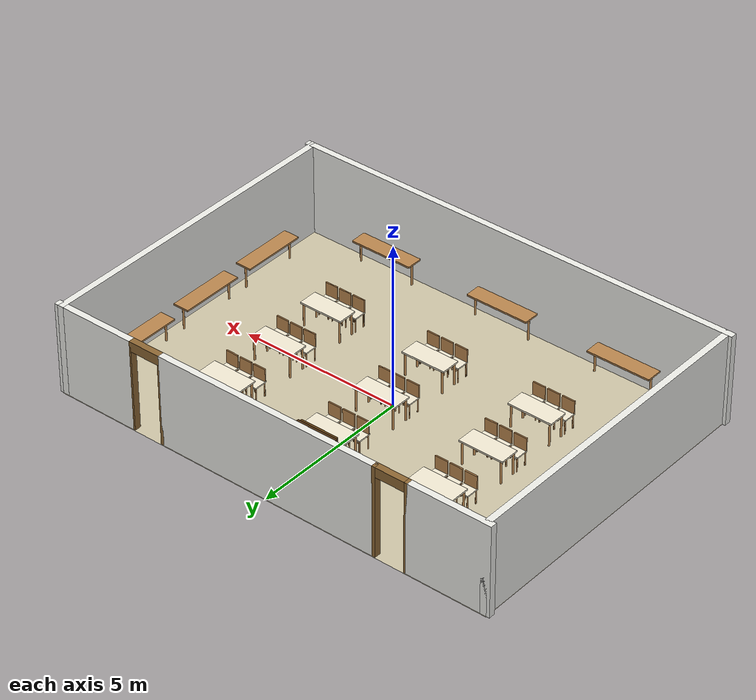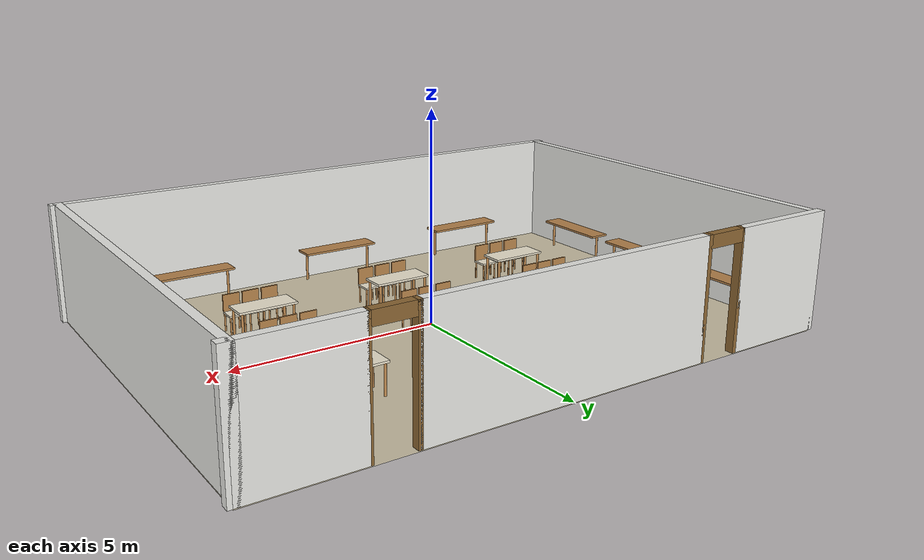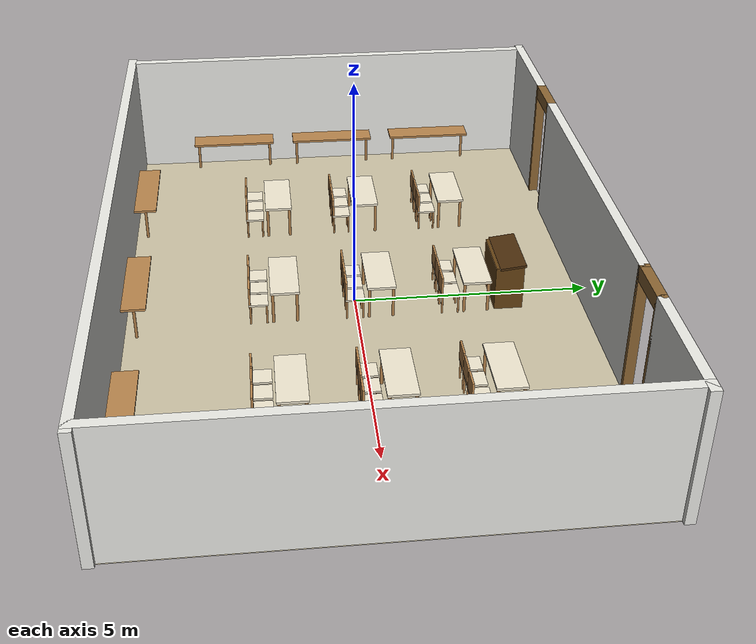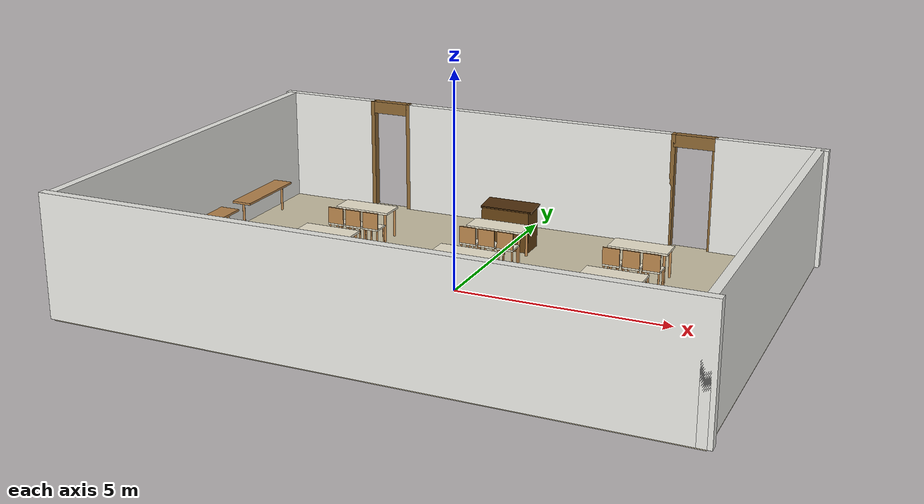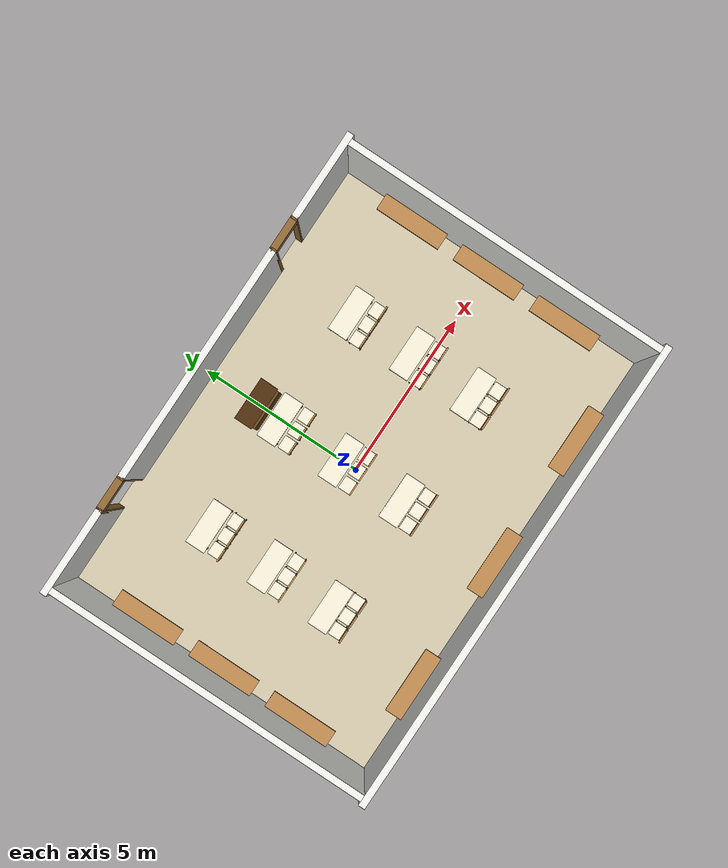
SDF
<?xml version="1.0" ?>
<!-- mecanum_classroom.world — Gazebo Harmonic classroom
     -->
<sdf version="1.10">
  <world name="mecanum_classroom">
    <physics name="1ms" type="ignored"><max_step_size>0.001</max_step_size><real_time_factor>1.0</real_time_factor></physics>
    <plugin filename="gz-sim-physics-system" name="gz::sim::systems::Physics"/>
    <plugin filename="gz-sim-user-commands-system" name="gz::sim::systems::UserCommands"/>
    <plugin filename="gz-sim-scene-broadcaster-system" name="gz::sim::systems::SceneBroadcaster"/>
    <plugin filename="gz-sim-contact-system" name="gz::sim::systems::Contact"/>
    <plugin filename="gz-sim-contact-system" name="gz::sim::systems::Contact" />
    <gui fullscreen="0">
      <plugin name="3D View" filename="gz-sim-gui-system">
        <render_engine>ogre</render_engine>
      </plugin>
    </gui>
    <plugin filename="gz-sim-sensors-system" name="gz::sim::systems::Sensors"><render_engine>ogre</render_engine></plugin>
    <scene><ambient>0.85 0.82 0.75 1</ambient><background>0.85 0.82 0.75 1</background><shadows>true</shadows></scene>
    <light name="ceiling_light" type="point"><cast_shadows>false</cast_shadows><pose>0 0 2.6 0 0 0</pose>
      <diffuse>1.0 0.97 0.88 1</diffuse><specular>0.3 0.3 0.3 1</specular>
      <attenuation><range>20</range><constant>0.4</constant><linear>0.05</linear><quadratic>0.002</quadratic></attenuation></light>
    <light name="north_fill" type="directional"><cast_shadows>true</cast_shadows><pose>0 4 2.5 0 0 0</pose>
      <diffuse>0.8 0.78 0.70 1</diffuse><specular>0.1 0.1 0.1 1</specular><direction>0.2 0.6 -0.8</direction></light>
    <model name="floor"><static>true</static><link name="link">
      <collision name="col"><geometry><plane><normal>0 0 1</normal><size>14 10</size></plane></geometry>
        <surface><friction><ode><mu>0.9</mu><mu2>0.9</mu2></ode></friction></surface></collision>
      <visual name="vis"><geometry><plane><normal>0 0 1</normal><size>14 10</size></plane></geometry>
        <material><ambient>0.80 0.76 0.65 1</ambient><diffuse>0.80 0.76 0.65 1</diffuse></material></visual>
    </link></model>
    <model name="wall_north_A"><static>true</static><pose>-5.8 4.9 1.4 0 0 0</pose>
      <link name="link">
        <collision name="col"><geometry><box><size>2.6 0.2 2.8</size></box></geometry></collision>
        <visual name="vis"><geometry><box><size>2.6 0.2 2.8</size></box></geometry>
          <material><ambient>0.92 0.92 0.90 1</ambient><diffuse>0.92 0.92 0.90 1</diffuse></material></visual>
      </link></model>
    <model name="wall_north_B"><static>true</static><pose>0.0 4.9 1.4 0 0 0</pose>
      <link name="link">
        <collision name="col"><geometry><box><size>7.0 0.2 2.8</size></box></geometry></collision>
        <visual name="vis"><geometry><box><size>7.0 0.2 2.8</size></box></geometry>
          <material><ambient>0.92 0.92 0.90 1</ambient><diffuse>0.92 0.92 0.90 1</diffuse></material></visual>
      </link></model>
    <model name="wall_north_C"><static>true</static><pose>5.8 4.9 1.4 0 0 0</pose>
      <link name="link">
        <collision name="col"><geometry><box><size>2.6 0.2 2.8</size></box></geometry></collision>
        <visual name="vis"><geometry><box><size>2.6 0.2 2.8</size></box></geometry>
          <material><ambient>0.92 0.92 0.90 1</ambient><diffuse>0.92 0.92 0.90 1</diffuse></material></visual>
      </link></model>
    <model name="wall_south"><static>true</static><pose>0.0 -4.9 1.4 0 0 0</pose>
      <link name="link">
        <collision name="col"><geometry><box><size>14.2 0.2 2.8</size></box></geometry></collision>
        <visual name="vis"><geometry><box><size>14.2 0.2 2.8</size></box></geometry>
          <material><ambient>0.92 0.92 0.90 1</ambient><diffuse>0.92 0.92 0.90 1</diffuse></material></visual>
      </link></model>
    <model name="wall_west"><static>true</static><pose>-6.9 0.0 1.4 0 0 0</pose>
      <link name="link">
        <collision name="col"><geometry><box><size>0.2 10.0 2.8</size></box></geometry></collision>
        <visual name="vis"><geometry><box><size>0.2 10.0 2.8</size></box></geometry>
          <material><ambient>0.92 0.92 0.90 1</ambient><diffuse>0.92 0.92 0.90 1</diffuse></material></visual>
      </link></model>
    <model name="wall_east"><static>true</static><pose>6.9 0.0 1.4 0 0 0</pose>
      <link name="link">
        <collision name="col"><geometry><box><size>0.2 10.0 2.8</size></box></geometry></collision>
        <visual name="vis"><geometry><box><size>0.2 10.0 2.8</size></box></geometry>
          <material><ambient>0.92 0.92 0.90 1</ambient><diffuse>0.92 0.92 0.90 1</diffuse></material></visual>
      </link></model>
    <model name="door_pillar_LL"><static>true</static><pose>-4.5 4.9 1.4 0 0 0</pose>
      <link name="link">
        <collision name="col"><geometry><box><size>0.1 0.2 2.8</size></box></geometry></collision>
        <visual name="vis"><geometry><box><size>0.1 0.2 2.8</size></box></geometry>
          <material><ambient>0.55 0.40 0.20 1</ambient><diffuse>0.55 0.40 0.20 1</diffuse></material></visual>
      </link></model>
    <model name="door_pillar_LR"><static>true</static><pose>-3.5 4.9 1.4 0 0 0</pose>
      <link name="link">
        <collision name="col"><geometry><box><size>0.1 0.2 2.8</size></box></geometry></collision>
        <visual name="vis"><geometry><box><size>0.1 0.2 2.8</size></box></geometry>
          <material><ambient>0.55 0.40 0.20 1</ambient><diffuse>0.55 0.40 0.20 1</diffuse></material></visual>
      </link></model>
    <model name="door_pillar_RL"><static>true</static><pose>3.5 4.9 1.4 0 0 0</pose>
      <link name="link">
        <collision name="col"><geometry><box><size>0.1 0.2 2.8</size></box></geometry></collision>
        <visual name="vis"><geometry><box><size>0.1 0.2 2.8</size></box></geometry>
          <material><ambient>0.55 0.40 0.20 1</ambient><diffuse>0.55 0.40 0.20 1</diffuse></material></visual>
      </link></model>
    <model name="door_pillar_RR"><static>true</static><pose>4.5 4.9 1.4 0 0 0</pose>
      <link name="link">
        <collision name="col"><geometry><box><size>0.1 0.2 2.8</size></box></geometry></collision>
        <visual name="vis"><geometry><box><size>0.1 0.2 2.8</size></box></geometry>
          <material><ambient>0.55 0.40 0.20 1</ambient><diffuse>0.55 0.40 0.20 1</diffuse></material></visual>
      </link></model>
    <model name="door_L_lintel"><static>true</static><pose>-4.0 4.9 2.65 0 0 0</pose>
      <link name="link">
        <collision name="col"><geometry><box><size>1.0 0.2 0.3</size></box></geometry></collision>
        <visual name="vis"><geometry><box><size>1.0 0.2 0.3</size></box></geometry>
          <material><ambient>0.55 0.40 0.20 1</ambient><diffuse>0.55 0.40 0.20 1</diffuse></material></visual>
      </link></model>
    <model name="door_R_lintel"><static>true</static><pose>4.0 4.9 2.65 0 0 0</pose>
      <link name="link">
        <collision name="col"><geometry><box><size>1.0 0.2 0.3</size></box></geometry></collision>
        <visual name="vis"><geometry><box><size>1.0 0.2 0.3</size></box></geometry>
          <material><ambient>0.55 0.40 0.20 1</ambient><diffuse>0.55 0.40 0.20 1</diffuse></material></visual>
      </link></model>
    <model name="teacher_stand_base"><static>true</static><pose>0 3.2 0.5 0 0 0</pose>
      <link name="link">
        <collision name="col"><geometry><box><size>1.2 0.6 1.0</size></box></geometry></collision>
        <visual name="vis"><geometry><box><size>1.2 0.6 1.0</size></box></geometry>
          <material><ambient>0.40 0.26 0.08 1</ambient><diffuse>0.40 0.26 0.08 1</diffuse></material></visual>
      </link></model>
    <model name="teacher_stand_top"><static>true</static><pose>0 3.25 1.02 0.12 0 0</pose>
      <link name="link">
        <collision name="col"><geometry><box><size>1.3 0.55 0.05</size></box></geometry></collision>
        <visual name="vis"><geometry><box><size>1.3 0.55 0.05</size></box></geometry>
          <material><ambient>0.30 0.18 0.05 1</ambient><diffuse>0.30 0.18 0.05 1</diffuse></material></visual>
      </link></model>
    <model name="tbl_r1c1_top"><static>true</static><pose>-3.5 2.5 0.73 0 0 0</pose>
      <link name="link">
        <collision name="col"><geometry><box><size>1.4 0.6 0.05</size></box></geometry></collision>
        <visual name="vis"><geometry><box><size>1.4 0.6 0.05</size></box></geometry>
          <material><ambient>0.94 0.91 0.82 1</ambient><diffuse>0.94 0.91 0.82 1</diffuse></material></visual>
      </link></model>
    <model name="tbl_r1c1_legs"><static>true</static><pose>-3.5 2.5 0.36 0 0 0</pose>
      <link name="link">
        <collision name="col"><geometry><box><size>1.4 0.6 0.72</size></box></geometry></collision>
        <visual name="leg_fl"><pose>-0.62 -0.25 0 0 0 0</pose><geometry><cylinder><radius>0.03</radius><length>0.72</length></cylinder></geometry>
          <material><ambient>0.72 0.52 0.30 1</ambient><diffuse>0.72 0.52 0.30 1</diffuse></material></visual>
        <visual name="leg_fr"><pose>0.62 -0.25 0 0 0 0</pose><geometry><cylinder><radius>0.03</radius><length>0.72</length></cylinder></geometry>
          <material><ambient>0.72 0.52 0.30 1</ambient><diffuse>0.72 0.52 0.30 1</diffuse></material></visual>
        <visual name="leg_bl"><pose>-0.62 0.25 0 0 0 0</pose><geometry><cylinder><radius>0.03</radius><length>0.72</length></cylinder></geometry>
          <material><ambient>0.72 0.52 0.30 1</ambient><diffuse>0.72 0.52 0.30 1</diffuse></material></visual>
        <visual name="leg_br"><pose>0.62 0.25 0 0 0 0</pose><geometry><cylinder><radius>0.03</radius><length>0.72</length></cylinder></geometry>
          <material><ambient>0.72 0.52 0.30 1</ambient><diffuse>0.72 0.52 0.30 1</diffuse></material></visual>
      </link></model>
    <model name="chr_r1c1_a"><static>true</static><pose>-3.97 1.95 0.45 0 0 0</pose>
      <link name="link">
        <visual name="seat"><geometry><box><size>0.40 0.40 0.04</size></box></geometry>
          <material><ambient>0.94 0.91 0.82 1</ambient><diffuse>0.94 0.91 0.82 1</diffuse></material></visual>
        <visual name="back"><pose>0 -0.18 0.22 0 0 0</pose><geometry><box><size>0.40 0.04 0.40</size></box></geometry>
          <material><ambient>0.72 0.52 0.30 1</ambient><diffuse>0.72 0.52 0.30 1</diffuse></material></visual>
        <visual name="leg_fl"><pose>-0.17 -0.17 -0.225 0 0 0</pose><geometry><cylinder><radius>0.02</radius><length>0.45</length></cylinder></geometry>
          <material><ambient>0.72 0.52 0.30 1</ambient><diffuse>0.72 0.52 0.30 1</diffuse></material></visual>
        <visual name="leg_fr"><pose>0.17 -0.17 -0.225 0 0 0</pose><geometry><cylinder><radius>0.02</radius><length>0.45</length></cylinder></geometry>
          <material><ambient>0.72 0.52 0.30 1</ambient><diffuse>0.72 0.52 0.30 1</diffuse></material></visual>
        <visual name="leg_bl"><pose>-0.17 0.17 -0.225 0 0 0</pose><geometry><cylinder><radius>0.02</radius><length>0.45</length></cylinder></geometry>
          <material><ambient>0.72 0.52 0.30 1</ambient><diffuse>0.72 0.52 0.30 1</diffuse></material></visual>
        <visual name="leg_br"><pose>0.17 0.17 -0.225 0 0 0</pose><geometry><cylinder><radius>0.02</radius><length>0.45</length></cylinder></geometry>
          <material><ambient>0.72 0.52 0.30 1</ambient><diffuse>0.72 0.52 0.30 1</diffuse></material></visual>
        <collision name="col"><geometry><box><size>0.40 0.40 0.04</size></box></geometry></collision>
      </link></model>
    <model name="chr_r1c1_b"><static>true</static><pose>-3.5 1.95 0.45 0 0 0</pose>
      <link name="link">
        <visual name="seat"><geometry><box><size>0.40 0.40 0.04</size></box></geometry>
          <material><ambient>0.94 0.91 0.82 1</ambient><diffuse>0.94 0.91 0.82 1</diffuse></material></visual>
        <visual name="back"><pose>0 -0.18 0.22 0 0 0</pose><geometry><box><size>0.40 0.04 0.40</size></box></geometry>
          <material><ambient>0.72 0.52 0.30 1</ambient><diffuse>0.72 0.52 0.30 1</diffuse></material></visual>
        <visual name="leg_fl"><pose>-0.17 -0.17 -0.225 0 0 0</pose><geometry><cylinder><radius>0.02</radius><length>0.45</length></cylinder></geometry>
          <material><ambient>0.72 0.52 0.30 1</ambient><diffuse>0.72 0.52 0.30 1</diffuse></material></visual>
        <visual name="leg_fr"><pose>0.17 -0.17 -0.225 0 0 0</pose><geometry><cylinder><radius>0.02</radius><length>0.45</length></cylinder></geometry>
          <material><ambient>0.72 0.52 0.30 1</ambient><diffuse>0.72 0.52 0.30 1</diffuse></material></visual>
        <visual name="leg_bl"><pose>-0.17 0.17 -0.225 0 0 0</pose><geometry><cylinder><radius>0.02</radius><length>0.45</length></cylinder></geometry>
          <material><ambient>0.72 0.52 0.30 1</ambient><diffuse>0.72 0.52 0.30 1</diffuse></material></visual>
        <visual name="leg_br"><pose>0.17 0.17 -0.225 0 0 0</pose><geometry><cylinder><radius>0.02</radius><length>0.45</length></cylinder></geometry>
          <material><ambient>0.72 0.52 0.30 1</ambient><diffuse>0.72 0.52 0.30 1</diffuse></material></visual>
        <collision name="col"><geometry><box><size>0.40 0.40 0.04</size></box></geometry></collision>
      </link></model>
    <model name="chr_r1c1_c"><static>true</static><pose>-3.03 1.95 0.45 0 0 0</pose>
      <link name="link">
        <visual name="seat"><geometry><box><size>0.40 0.40 0.04</size></box></geometry>
          <material><ambient>0.94 0.91 0.82 1</ambient><diffuse>0.94 0.91 0.82 1</diffuse></material></visual>
        <visual name="back"><pose>0 -0.18 0.22 0 0 0</pose><geometry><box><size>0.40 0.04 0.40</size></box></geometry>
          <material><ambient>0.72 0.52 0.30 1</ambient><diffuse>0.72 0.52 0.30 1</diffuse></material></visual>
        <visual name="leg_fl"><pose>-0.17 -0.17 -0.225 0 0 0</pose><geometry><cylinder><radius>0.02</radius><length>0.45</length></cylinder></geometry>
          <material><ambient>0.72 0.52 0.30 1</ambient><diffuse>0.72 0.52 0.30 1</diffuse></material></visual>
        <visual name="leg_fr"><pose>0.17 -0.17 -0.225 0 0 0</pose><geometry><cylinder><radius>0.02</radius><length>0.45</length></cylinder></geometry>
          <material><ambient>0.72 0.52 0.30 1</ambient><diffuse>0.72 0.52 0.30 1</diffuse></material></visual>
        <visual name="leg_bl"><pose>-0.17 0.17 -0.225 0 0 0</pose><geometry><cylinder><radius>0.02</radius><length>0.45</length></cylinder></geometry>
          <material><ambient>0.72 0.52 0.30 1</ambient><diffuse>0.72 0.52 0.30 1</diffuse></material></visual>
        <visual name="leg_br"><pose>0.17 0.17 -0.225 0 0 0</pose><geometry><cylinder><radius>0.02</radius><length>0.45</length></cylinder></geometry>
          <material><ambient>0.72 0.52 0.30 1</ambient><diffuse>0.72 0.52 0.30 1</diffuse></material></visual>
        <collision name="col"><geometry><box><size>0.40 0.40 0.04</size></box></geometry></collision>
      </link></model>
    <model name="tbl_r1c2_top"><static>true</static><pose>0.0 2.5 0.73 0 0 0</pose>
      <link name="link">
        <collision name="col"><geometry><box><size>1.4 0.6 0.05</size></box></geometry></collision>
        <visual name="vis"><geometry><box><size>1.4 0.6 0.05</size></box></geometry>
          <material><ambient>0.94 0.91 0.82 1</ambient><diffuse>0.94 0.91 0.82 1</diffuse></material></visual>
      </link></model>
    <model name="tbl_r1c2_legs"><static>true</static><pose>0.0 2.5 0.36 0 0 0</pose>
      <link name="link">
        <collision name="col"><geometry><box><size>1.4 0.6 0.72</size></box></geometry></collision>
        <visual name="leg_fl"><pose>-0.62 -0.25 0 0 0 0</pose><geometry><cylinder><radius>0.03</radius><length>0.72</length></cylinder></geometry>
          <material><ambient>0.72 0.52 0.30 1</ambient><diffuse>0.72 0.52 0.30 1</diffuse></material></visual>
        <visual name="leg_fr"><pose>0.62 -0.25 0 0 0 0</pose><geometry><cylinder><radius>0.03</radius><length>0.72</length></cylinder></geometry>
          <material><ambient>0.72 0.52 0.30 1</ambient><diffuse>0.72 0.52 0.30 1</diffuse></material></visual>
        <visual name="leg_bl"><pose>-0.62 0.25 0 0 0 0</pose><geometry><cylinder><radius>0.03</radius><length>0.72</length></cylinder></geometry>
          <material><ambient>0.72 0.52 0.30 1</ambient><diffuse>0.72 0.52 0.30 1</diffuse></material></visual>
        <visual name="leg_br"><pose>0.62 0.25 0 0 0 0</pose><geometry><cylinder><radius>0.03</radius><length>0.72</length></cylinder></geometry>
          <material><ambient>0.72 0.52 0.30 1</ambient><diffuse>0.72 0.52 0.30 1</diffuse></material></visual>
      </link></model>
    <model name="chr_r1c2_a"><static>true</static><pose>-0.47 1.95 0.45 0 0 0</pose>
      <link name="link">
        <visual name="seat"><geometry><box><size>0.40 0.40 0.04</size></box></geometry>
          <material><ambient>0.94 0.91 0.82 1</ambient><diffuse>0.94 0.91 0.82 1</diffuse></material></visual>
        <visual name="back"><pose>0 -0.18 0.22 0 0 0</pose><geometry><box><size>0.40 0.04 0.40</size></box></geometry>
          <material><ambient>0.72 0.52 0.30 1</ambient><diffuse>0.72 0.52 0.30 1</diffuse></material></visual>
        <visual name="leg_fl"><pose>-0.17 -0.17 -0.225 0 0 0</pose><geometry><cylinder><radius>0.02</radius><length>0.45</length></cylinder></geometry>
          <material><ambient>0.72 0.52 0.30 1</ambient><diffuse>0.72 0.52 0.30 1</diffuse></material></visual>
        <visual name="leg_fr"><pose>0.17 -0.17 -0.225 0 0 0</pose><geometry><cylinder><radius>0.02</radius><length>0.45</length></cylinder></geometry>
          <material><ambient>0.72 0.52 0.30 1</ambient><diffuse>0.72 0.52 0.30 1</diffuse></material></visual>
        <visual name="leg_bl"><pose>-0.17 0.17 -0.225 0 0 0</pose><geometry><cylinder><radius>0.02</radius><length>0.45</length></cylinder></geometry>
          <material><ambient>0.72 0.52 0.30 1</ambient><diffuse>0.72 0.52 0.30 1</diffuse></material></visual>
        <visual name="leg_br"><pose>0.17 0.17 -0.225 0 0 0</pose><geometry><cylinder><radius>0.02</radius><length>0.45</length></cylinder></geometry>
          <material><ambient>0.72 0.52 0.30 1</ambient><diffuse>0.72 0.52 0.30 1</diffuse></material></visual>
        <collision name="col"><geometry><box><size>0.40 0.40 0.04</size></box></geometry></collision>
      </link></model>
    <model name="chr_r1c2_b"><static>true</static><pose>0.0 1.95 0.45 0 0 0</pose>
      <link name="link">
        <visual name="seat"><geometry><box><size>0.40 0.40 0.04</size></box></geometry>
          <material><ambient>0.94 0.91 0.82 1</ambient><diffuse>0.94 0.91 0.82 1</diffuse></material></visual>
        <visual name="back"><pose>0 -0.18 0.22 0 0 0</pose><geometry><box><size>0.40 0.04 0.40</size></box></geometry>
          <material><ambient>0.72 0.52 0.30 1</ambient><diffuse>0.72 0.52 0.30 1</diffuse></material></visual>
        <visual name="leg_fl"><pose>-0.17 -0.17 -0.225 0 0 0</pose><geometry><cylinder><radius>0.02</radius><length>0.45</length></cylinder></geometry>
          <material><ambient>0.72 0.52 0.30 1</ambient><diffuse>0.72 0.52 0.30 1</diffuse></material></visual>
        <visual name="leg_fr"><pose>0.17 -0.17 -0.225 0 0 0</pose><geometry><cylinder><radius>0.02</radius><length>0.45</length></cylinder></geometry>
          <material><ambient>0.72 0.52 0.30 1</ambient><diffuse>0.72 0.52 0.30 1</diffuse></material></visual>
        <visual name="leg_bl"><pose>-0.17 0.17 -0.225 0 0 0</pose><geometry><cylinder><radius>0.02</radius><length>0.45</length></cylinder></geometry>
          <material><ambient>0.72 0.52 0.30 1</ambient><diffuse>0.72 0.52 0.30 1</diffuse></material></visual>
        <visual name="leg_br"><pose>0.17 0.17 -0.225 0 0 0</pose><geometry><cylinder><radius>0.02</radius><length>0.45</length></cylinder></geometry>
          <material><ambient>0.72 0.52 0.30 1</ambient><diffuse>0.72 0.52 0.30 1</diffuse></material></visual>
        <collision name="col"><geometry><box><size>0.40 0.40 0.04</size></box></geometry></collision>
      </link></model>
    <model name="chr_r1c2_c"><static>true</static><pose>0.47 1.95 0.45 0 0 0</pose>
      <link name="link">
        <visual name="seat"><geometry><box><size>0.40 0.40 0.04</size></box></geometry>
          <material><ambient>0.94 0.91 0.82 1</ambient><diffuse>0.94 0.91 0.82 1</diffuse></material></visual>
        <visual name="back"><pose>0 -0.18 0.22 0 0 0</pose><geometry><box><size>0.40 0.04 0.40</size></box></geometry>
          <material><ambient>0.72 0.52 0.30 1</ambient><diffuse>0.72 0.52 0.30 1</diffuse></material></visual>
        <visual name="leg_fl"><pose>-0.17 -0.17 -0.225 0 0 0</pose><geometry><cylinder><radius>0.02</radius><length>0.45</length></cylinder></geometry>
          <material><ambient>0.72 0.52 0.30 1</ambient><diffuse>0.72 0.52 0.30 1</diffuse></material></visual>
        <visual name="leg_fr"><pose>0.17 -0.17 -0.225 0 0 0</pose><geometry><cylinder><radius>0.02</radius><length>0.45</length></cylinder></geometry>
          <material><ambient>0.72 0.52 0.30 1</ambient><diffuse>0.72 0.52 0.30 1</diffuse></material></visual>
        <visual name="leg_bl"><pose>-0.17 0.17 -0.225 0 0 0</pose><geometry><cylinder><radius>0.02</radius><length>0.45</length></cylinder></geometry>
          <material><ambient>0.72 0.52 0.30 1</ambient><diffuse>0.72 0.52 0.30 1</diffuse></material></visual>
        <visual name="leg_br"><pose>0.17 0.17 -0.225 0 0 0</pose><geometry><cylinder><radius>0.02</radius><length>0.45</length></cylinder></geometry>
          <material><ambient>0.72 0.52 0.30 1</ambient><diffuse>0.72 0.52 0.30 1</diffuse></material></visual>
        <collision name="col"><geometry><box><size>0.40 0.40 0.04</size></box></geometry></collision>
      </link></model>
    <model name="tbl_r1c3_top"><static>true</static><pose>3.5 2.5 0.73 0 0 0</pose>
      <link name="link">
        <collision name="col"><geometry><box><size>1.4 0.6 0.05</size></box></geometry></collision>
        <visual name="vis"><geometry><box><size>1.4 0.6 0.05</size></box></geometry>
          <material><ambient>0.94 0.91 0.82 1</ambient><diffuse>0.94 0.91 0.82 1</diffuse></material></visual>
      </link></model>
    <model name="tbl_r1c3_legs"><static>true</static><pose>3.5 2.5 0.36 0 0 0</pose>
      <link name="link">
        <collision name="col"><geometry><box><size>1.4 0.6 0.72</size></box></geometry></collision>
        <visual name="leg_fl"><pose>-0.62 -0.25 0 0 0 0</pose><geometry><cylinder><radius>0.03</radius><length>0.72</length></cylinder></geometry>
          <material><ambient>0.72 0.52 0.30 1</ambient><diffuse>0.72 0.52 0.30 1</diffuse></material></visual>
        <visual name="leg_fr"><pose>0.62 -0.25 0 0 0 0</pose><geometry><cylinder><radius>0.03</radius><length>0.72</length></cylinder></geometry>
          <material><ambient>0.72 0.52 0.30 1</ambient><diffuse>0.72 0.52 0.30 1</diffuse></material></visual>
        <visual name="leg_bl"><pose>-0.62 0.25 0 0 0 0</pose><geometry><cylinder><radius>0.03</radius><length>0.72</length></cylinder></geometry>
          <material><ambient>0.72 0.52 0.30 1</ambient><diffuse>0.72 0.52 0.30 1</diffuse></material></visual>
        <visual name="leg_br"><pose>0.62 0.25 0 0 0 0</pose><geometry><cylinder><radius>0.03</radius><length>0.72</length></cylinder></geometry>
          <material><ambient>0.72 0.52 0.30 1</ambient><diffuse>0.72 0.52 0.30 1</diffuse></material></visual>
      </link></model>
    <model name="chr_r1c3_a"><static>true</static><pose>3.03 1.95 0.45 0 0 0</pose>
      <link name="link">
        <visual name="seat"><geometry><box><size>0.40 0.40 0.04</size></box></geometry>
          <material><ambient>0.94 0.91 0.82 1</ambient><diffuse>0.94 0.91 0.82 1</diffuse></material></visual>
        <visual name="back"><pose>0 -0.18 0.22 0 0 0</pose><geometry><box><size>0.40 0.04 0.40</size></box></geometry>
          <material><ambient>0.72 0.52 0.30 1</ambient><diffuse>0.72 0.52 0.30 1</diffuse></material></visual>
        <visual name="leg_fl"><pose>-0.17 -0.17 -0.225 0 0 0</pose><geometry><cylinder><radius>0.02</radius><length>0.45</length></cylinder></geometry>
          <material><ambient>0.72 0.52 0.30 1</ambient><diffuse>0.72 0.52 0.30 1</diffuse></material></visual>
        <visual name="leg_fr"><pose>0.17 -0.17 -0.225 0 0 0</pose><geometry><cylinder><radius>0.02</radius><length>0.45</length></cylinder></geometry>
          <material><ambient>0.72 0.52 0.30 1</ambient><diffuse>0.72 0.52 0.30 1</diffuse></material></visual>
        <visual name="leg_bl"><pose>-0.17 0.17 -0.225 0 0 0</pose><geometry><cylinder><radius>0.02</radius><length>0.45</length></cylinder></geometry>
          <material><ambient>0.72 0.52 0.30 1</ambient><diffuse>0.72 0.52 0.30 1</diffuse></material></visual>
        <visual name="leg_br"><pose>0.17 0.17 -0.225 0 0 0</pose><geometry><cylinder><radius>0.02</radius><length>0.45</length></cylinder></geometry>
          <material><ambient>0.72 0.52 0.30 1</ambient><diffuse>0.72 0.52 0.30 1</diffuse></material></visual>
        <collision name="col"><geometry><box><size>0.40 0.40 0.04</size></box></geometry></collision>
      </link></model>
    <model name="chr_r1c3_b"><static>true</static><pose>3.5 1.95 0.45 0 0 0</pose>
      <link name="link">
        <visual name="seat"><geometry><box><size>0.40 0.40 0.04</size></box></geometry>
          <material><ambient>0.94 0.91 0.82 1</ambient><diffuse>0.94 0.91 0.82 1</diffuse></material></visual>
        <visual name="back"><pose>0 -0.18 0.22 0 0 0</pose><geometry><box><size>0.40 0.04 0.40</size></box></geometry>
          <material><ambient>0.72 0.52 0.30 1</ambient><diffuse>0.72 0.52 0.30 1</diffuse></material></visual>
        <visual name="leg_fl"><pose>-0.17 -0.17 -0.225 0 0 0</pose><geometry><cylinder><radius>0.02</radius><length>0.45</length></cylinder></geometry>
          <material><ambient>0.72 0.52 0.30 1</ambient><diffuse>0.72 0.52 0.30 1</diffuse></material></visual>
        <visual name="leg_fr"><pose>0.17 -0.17 -0.225 0 0 0</pose><geometry><cylinder><radius>0.02</radius><length>0.45</length></cylinder></geometry>
          <material><ambient>0.72 0.52 0.30 1</ambient><diffuse>0.72 0.52 0.30 1</diffuse></material></visual>
        <visual name="leg_bl"><pose>-0.17 0.17 -0.225 0 0 0</pose><geometry><cylinder><radius>0.02</radius><length>0.45</length></cylinder></geometry>
          <material><ambient>0.72 0.52 0.30 1</ambient><diffuse>0.72 0.52 0.30 1</diffuse></material></visual>
        <visual name="leg_br"><pose>0.17 0.17 -0.225 0 0 0</pose><geometry><cylinder><radius>0.02</radius><length>0.45</length></cylinder></geometry>
          <material><ambient>0.72 0.52 0.30 1</ambient><diffuse>0.72 0.52 0.30 1</diffuse></material></visual>
        <collision name="col"><geometry><box><size>0.40 0.40 0.04</size></box></geometry></collision>
      </link></model>
    <model name="chr_r1c3_c"><static>true</static><pose>3.97 1.95 0.45 0 0 0</pose>
      <link name="link">
        <visual name="seat"><geometry><box><size>0.40 0.40 0.04</size></box></geometry>
          <material><ambient>0.94 0.91 0.82 1</ambient><diffuse>0.94 0.91 0.82 1</diffuse></material></visual>
        <visual name="back"><pose>0 -0.18 0.22 0 0 0</pose><geometry><box><size>0.40 0.04 0.40</size></box></geometry>
          <material><ambient>0.72 0.52 0.30 1</ambient><diffuse>0.72 0.52 0.30 1</diffuse></material></visual>
        <visual name="leg_fl"><pose>-0.17 -0.17 -0.225 0 0 0</pose><geometry><cylinder><radius>0.02</radius><length>0.45</length></cylinder></geometry>
          <material><ambient>0.72 0.52 0.30 1</ambient><diffuse>0.72 0.52 0.30 1</diffuse></material></visual>
        <visual name="leg_fr"><pose>0.17 -0.17 -0.225 0 0 0</pose><geometry><cylinder><radius>0.02</radius><length>0.45</length></cylinder></geometry>
          <material><ambient>0.72 0.52 0.30 1</ambient><diffuse>0.72 0.52 0.30 1</diffuse></material></visual>
        <visual name="leg_bl"><pose>-0.17 0.17 -0.225 0 0 0</pose><geometry><cylinder><radius>0.02</radius><length>0.45</length></cylinder></geometry>
          <material><ambient>0.72 0.52 0.30 1</ambient><diffuse>0.72 0.52 0.30 1</diffuse></material></visual>
        <visual name="leg_br"><pose>0.17 0.17 -0.225 0 0 0</pose><geometry><cylinder><radius>0.02</radius><length>0.45</length></cylinder></geometry>
          <material><ambient>0.72 0.52 0.30 1</ambient><diffuse>0.72 0.52 0.30 1</diffuse></material></visual>
        <collision name="col"><geometry><box><size>0.40 0.40 0.04</size></box></geometry></collision>
      </link></model>
    <model name="tbl_r2c1_top"><static>true</static><pose>-3.5 0.5 0.73 0 0 0</pose>
      <link name="link">
        <collision name="col"><geometry><box><size>1.4 0.6 0.05</size></box></geometry></collision>
        <visual name="vis"><geometry><box><size>1.4 0.6 0.05</size></box></geometry>
          <material><ambient>0.94 0.91 0.82 1</ambient><diffuse>0.94 0.91 0.82 1</diffuse></material></visual>
      </link></model>
    <model name="tbl_r2c1_legs"><static>true</static><pose>-3.5 0.5 0.36 0 0 0</pose>
      <link name="link">
        <collision name="col"><geometry><box><size>1.4 0.6 0.72</size></box></geometry></collision>
        <visual name="leg_fl"><pose>-0.62 -0.25 0 0 0 0</pose><geometry><cylinder><radius>0.03</radius><length>0.72</length></cylinder></geometry>
          <material><ambient>0.72 0.52 0.30 1</ambient><diffuse>0.72 0.52 0.30 1</diffuse></material></visual>
        <visual name="leg_fr"><pose>0.62 -0.25 0 0 0 0</pose><geometry><cylinder><radius>0.03</radius><length>0.72</length></cylinder></geometry>
          <material><ambient>0.72 0.52 0.30 1</ambient><diffuse>0.72 0.52 0.30 1</diffuse></material></visual>
        <visual name="leg_bl"><pose>-0.62 0.25 0 0 0 0</pose><geometry><cylinder><radius>0.03</radius><length>0.72</length></cylinder></geometry>
          <material><ambient>0.72 0.52 0.30 1</ambient><diffuse>0.72 0.52 0.30 1</diffuse></material></visual>
        <visual name="leg_br"><pose>0.62 0.25 0 0 0 0</pose><geometry><cylinder><radius>0.03</radius><length>0.72</length></cylinder></geometry>
          <material><ambient>0.72 0.52 0.30 1</ambient><diffuse>0.72 0.52 0.30 1</diffuse></material></visual>
      </link></model>
    <model name="chr_r2c1_a"><static>true</static><pose>-3.97 -0.05 0.45 0 0 0</pose>
      <link name="link">
        <visual name="seat"><geometry><box><size>0.40 0.40 0.04</size></box></geometry>
          <material><ambient>0.94 0.91 0.82 1</ambient><diffuse>0.94 0.91 0.82 1</diffuse></material></visual>
        <visual name="back"><pose>0 -0.18 0.22 0 0 0</pose><geometry><box><size>0.40 0.04 0.40</size></box></geometry>
          <material><ambient>0.72 0.52 0.30 1</ambient><diffuse>0.72 0.52 0.30 1</diffuse></material></visual>
        <visual name="leg_fl"><pose>-0.17 -0.17 -0.225 0 0 0</pose><geometry><cylinder><radius>0.02</radius><length>0.45</length></cylinder></geometry>
          <material><ambient>0.72 0.52 0.30 1</ambient><diffuse>0.72 0.52 0.30 1</diffuse></material></visual>
        <visual name="leg_fr"><pose>0.17 -0.17 -0.225 0 0 0</pose><geometry><cylinder><radius>0.02</radius><length>0.45</length></cylinder></geometry>
          <material><ambient>0.72 0.52 0.30 1</ambient><diffuse>0.72 0.52 0.30 1</diffuse></material></visual>
        <visual name="leg_bl"><pose>-0.17 0.17 -0.225 0 0 0</pose><geometry><cylinder><radius>0.02</radius><length>0.45</length></cylinder></geometry>
          <material><ambient>0.72 0.52 0.30 1</ambient><diffuse>0.72 0.52 0.30 1</diffuse></material></visual>
        <visual name="leg_br"><pose>0.17 0.17 -0.225 0 0 0</pose><geometry><cylinder><radius>0.02</radius><length>0.45</length></cylinder></geometry>
          <material><ambient>0.72 0.52 0.30 1</ambient><diffuse>0.72 0.52 0.30 1</diffuse></material></visual>
        <collision name="col"><geometry><box><size>0.40 0.40 0.04</size></box></geometry></collision>
      </link></model>
    <model name="chr_r2c1_b"><static>true</static><pose>-3.5 -0.05 0.45 0 0 0</pose>
      <link name="link">
        <visual name="seat"><geometry><box><size>0.40 0.40 0.04</size></box></geometry>
          <material><ambient>0.94 0.91 0.82 1</ambient><diffuse>0.94 0.91 0.82 1</diffuse></material></visual>
        <visual name="back"><pose>0 -0.18 0.22 0 0 0</pose><geometry><box><size>0.40 0.04 0.40</size></box></geometry>
          <material><ambient>0.72 0.52 0.30 1</ambient><diffuse>0.72 0.52 0.30 1</diffuse></material></visual>
        <visual name="leg_fl"><pose>-0.17 -0.17 -0.225 0 0 0</pose><geometry><cylinder><radius>0.02</radius><length>0.45</length></cylinder></geometry>
          <material><ambient>0.72 0.52 0.30 1</ambient><diffuse>0.72 0.52 0.30 1</diffuse></material></visual>
        <visual name="leg_fr"><pose>0.17 -0.17 -0.225 0 0 0</pose><geometry><cylinder><radius>0.02</radius><length>0.45</length></cylinder></geometry>
          <material><ambient>0.72 0.52 0.30 1</ambient><diffuse>0.72 0.52 0.30 1</diffuse></material></visual>
        <visual name="leg_bl"><pose>-0.17 0.17 -0.225 0 0 0</pose><geometry><cylinder><radius>0.02</radius><length>0.45</length></cylinder></geometry>
          <material><ambient>0.72 0.52 0.30 1</ambient><diffuse>0.72 0.52 0.30 1</diffuse></material></visual>
        <visual name="leg_br"><pose>0.17 0.17 -0.225 0 0 0</pose><geometry><cylinder><radius>0.02</radius><length>0.45</length></cylinder></geometry>
          <material><ambient>0.72 0.52 0.30 1</ambient><diffuse>0.72 0.52 0.30 1</diffuse></material></visual>
        <collision name="col"><geometry><box><size>0.40 0.40 0.04</size></box></geometry></collision>
      </link></model>
    <model name="chr_r2c1_c"><static>true</static><pose>-3.03 -0.05 0.45 0 0 0</pose>
      <link name="link">
        <visual name="seat"><geometry><box><size>0.40 0.40 0.04</size></box></geometry>
          <material><ambient>0.94 0.91 0.82 1</ambient><diffuse>0.94 0.91 0.82 1</diffuse></material></visual>
        <visual name="back"><pose>0 -0.18 0.22 0 0 0</pose><geometry><box><size>0.40 0.04 0.40</size></box></geometry>
          <material><ambient>0.72 0.52 0.30 1</ambient><diffuse>0.72 0.52 0.30 1</diffuse></material></visual>
        <visual name="leg_fl"><pose>-0.17 -0.17 -0.225 0 0 0</pose><geometry><cylinder><radius>0.02</radius><length>0.45</length></cylinder></geometry>
          <material><ambient>0.72 0.52 0.30 1</ambient><diffuse>0.72 0.52 0.30 1</diffuse></material></visual>
        <visual name="leg_fr"><pose>0.17 -0.17 -0.225 0 0 0</pose><geometry><cylinder><radius>0.02</radius><length>0.45</length></cylinder></geometry>
          <material><ambient>0.72 0.52 0.30 1</ambient><diffuse>0.72 0.52 0.30 1</diffuse></material></visual>
        <visual name="leg_bl"><pose>-0.17 0.17 -0.225 0 0 0</pose><geometry><cylinder><radius>0.02</radius><length>0.45</length></cylinder></geometry>
          <material><ambient>0.72 0.52 0.30 1</ambient><diffuse>0.72 0.52 0.30 1</diffuse></material></visual>
        <visual name="leg_br"><pose>0.17 0.17 -0.225 0 0 0</pose><geometry><cylinder><radius>0.02</radius><length>0.45</length></cylinder></geometry>
          <material><ambient>0.72 0.52 0.30 1</ambient><diffuse>0.72 0.52 0.30 1</diffuse></material></visual>
        <collision name="col"><geometry><box><size>0.40 0.40 0.04</size></box></geometry></collision>
      </link></model>
    <model name="tbl_r2c2_top"><static>true</static><pose>0.0 0.5 0.73 0 0 0</pose>
      <link name="link">
        <collision name="col"><geometry><box><size>1.4 0.6 0.05</size></box></geometry></collision>
        <visual name="vis"><geometry><box><size>1.4 0.6 0.05</size></box></geometry>
          <material><ambient>0.94 0.91 0.82 1</ambient><diffuse>0.94 0.91 0.82 1</diffuse></material></visual>
      </link></model>
    <model name="tbl_r2c2_legs"><static>true</static><pose>0.0 0.5 0.36 0 0 0</pose>
      <link name="link">
        <collision name="col"><geometry><box><size>1.4 0.6 0.72</size></box></geometry></collision>
        <visual name="leg_fl"><pose>-0.62 -0.25 0 0 0 0</pose><geometry><cylinder><radius>0.03</radius><length>0.72</length></cylinder></geometry>
          <material><ambient>0.72 0.52 0.30 1</ambient><diffuse>0.72 0.52 0.30 1</diffuse></material></visual>
        <visual name="leg_fr"><pose>0.62 -0.25 0 0 0 0</pose><geometry><cylinder><radius>0.03</radius><length>0.72</length></cylinder></geometry>
          <material><ambient>0.72 0.52 0.30 1</ambient><diffuse>0.72 0.52 0.30 1</diffuse></material></visual>
        <visual name="leg_bl"><pose>-0.62 0.25 0 0 0 0</pose><geometry><cylinder><radius>0.03</radius><length>0.72</length></cylinder></geometry>
          <material><ambient>0.72 0.52 0.30 1</ambient><diffuse>0.72 0.52 0.30 1</diffuse></material></visual>
        <visual name="leg_br"><pose>0.62 0.25 0 0 0 0</pose><geometry><cylinder><radius>0.03</radius><length>0.72</length></cylinder></geometry>
          <material><ambient>0.72 0.52 0.30 1</ambient><diffuse>0.72 0.52 0.30 1</diffuse></material></visual>
      </link></model>
    <model name="chr_r2c2_a"><static>true</static><pose>-0.47 -0.05 0.45 0 0 0</pose>
      <link name="link">
        <visual name="seat"><geometry><box><size>0.40 0.40 0.04</size></box></geometry>
          <material><ambient>0.94 0.91 0.82 1</ambient><diffuse>0.94 0.91 0.82 1</diffuse></material></visual>
        <visual name="back"><pose>0 -0.18 0.22 0 0 0</pose><geometry><box><size>0.40 0.04 0.40</size></box></geometry>
          <material><ambient>0.72 0.52 0.30 1</ambient><diffuse>0.72 0.52 0.30 1</diffuse></material></visual>
        <visual name="leg_fl"><pose>-0.17 -0.17 -0.225 0 0 0</pose><geometry><cylinder><radius>0.02</radius><length>0.45</length></cylinder></geometry>
          <material><ambient>0.72 0.52 0.30 1</ambient><diffuse>0.72 0.52 0.30 1</diffuse></material></visual>
        <visual name="leg_fr"><pose>0.17 -0.17 -0.225 0 0 0</pose><geometry><cylinder><radius>0.02</radius><length>0.45</length></cylinder></geometry>
          <material><ambient>0.72 0.52 0.30 1</ambient><diffuse>0.72 0.52 0.30 1</diffuse></material></visual>
        <visual name="leg_bl"><pose>-0.17 0.17 -0.225 0 0 0</pose><geometry><cylinder><radius>0.02</radius><length>0.45</length></cylinder></geometry>
          <material><ambient>0.72 0.52 0.30 1</ambient><diffuse>0.72 0.52 0.30 1</diffuse></material></visual>
        <visual name="leg_br"><pose>0.17 0.17 -0.225 0 0 0</pose><geometry><cylinder><radius>0.02</radius><length>0.45</length></cylinder></geometry>
          <material><ambient>0.72 0.52 0.30 1</ambient><diffuse>0.72 0.52 0.30 1</diffuse></material></visual>
        <collision name="col"><geometry><box><size>0.40 0.40 0.04</size></box></geometry></collision>
      </link></model>
    <model name="chr_r2c2_b"><static>true</static><pose>0.0 -0.05 0.45 0 0 0</pose>
      <link name="link">
        <visual name="seat"><geometry><box><size>0.40 0.40 0.04</size></box></geometry>
          <material><ambient>0.94 0.91 0.82 1</ambient><diffuse>0.94 0.91 0.82 1</diffuse></material></visual>
        <visual name="back"><pose>0 -0.18 0.22 0 0 0</pose><geometry><box><size>0.40 0.04 0.40</size></box></geometry>
          <material><ambient>0.72 0.52 0.30 1</ambient><diffuse>0.72 0.52 0.30 1</diffuse></material></visual>
        <visual name="leg_fl"><pose>-0.17 -0.17 -0.225 0 0 0</pose><geometry><cylinder><radius>0.02</radius><length>0.45</length></cylinder></geometry>
          <material><ambient>0.72 0.52 0.30 1</ambient><diffuse>0.72 0.52 0.30 1</diffuse></material></visual>
        <visual name="leg_fr"><pose>0.17 -0.17 -0.225 0 0 0</pose><geometry><cylinder><radius>0.02</radius><length>0.45</length></cylinder></geometry>
          <material><ambient>0.72 0.52 0.30 1</ambient><diffuse>0.72 0.52 0.30 1</diffuse></material></visual>
        <visual name="leg_bl"><pose>-0.17 0.17 -0.225 0 0 0</pose><geometry><cylinder><radius>0.02</radius><length>0.45</length></cylinder></geometry>
          <material><ambient>0.72 0.52 0.30 1</ambient><diffuse>0.72 0.52 0.30 1</diffuse></material></visual>
        <visual name="leg_br"><pose>0.17 0.17 -0.225 0 0 0</pose><geometry><cylinder><radius>0.02</radius><length>0.45</length></cylinder></geometry>
          <material><ambient>0.72 0.52 0.30 1</ambient><diffuse>0.72 0.52 0.30 1</diffuse></material></visual>
        <collision name="col"><geometry><box><size>0.40 0.40 0.04</size></box></geometry></collision>
      </link></model>
    <model name="chr_r2c2_c"><static>true</static><pose>0.47 -0.05 0.45 0 0 0</pose>
      <link name="link">
        <visual name="seat"><geometry><box><size>0.40 0.40 0.04</size></box></geometry>
          <material><ambient>0.94 0.91 0.82 1</ambient><diffuse>0.94 0.91 0.82 1</diffuse></material></visual>
        <visual name="back"><pose>0 -0.18 0.22 0 0 0</pose><geometry><box><size>0.40 0.04 0.40</size></box></geometry>
          <material><ambient>0.72 0.52 0.30 1</ambient><diffuse>0.72 0.52 0.30 1</diffuse></material></visual>
        <visual name="leg_fl"><pose>-0.17 -0.17 -0.225 0 0 0</pose><geometry><cylinder><radius>0.02</radius><length>0.45</length></cylinder></geometry>
          <material><ambient>0.72 0.52 0.30 1</ambient><diffuse>0.72 0.52 0.30 1</diffuse></material></visual>
        <visual name="leg_fr"><pose>0.17 -0.17 -0.225 0 0 0</pose><geometry><cylinder><radius>0.02</radius><length>0.45</length></cylinder></geometry>
          <material><ambient>0.72 0.52 0.30 1</ambient><diffuse>0.72 0.52 0.30 1</diffuse></material></visual>
        <visual name="leg_bl"><pose>-0.17 0.17 -0.225 0 0 0</pose><geometry><cylinder><radius>0.02</radius><length>0.45</length></cylinder></geometry>
          <material><ambient>0.72 0.52 0.30 1</ambient><diffuse>0.72 0.52 0.30 1</diffuse></material></visual>
        <visual name="leg_br"><pose>0.17 0.17 -0.225 0 0 0</pose><geometry><cylinder><radius>0.02</radius><length>0.45</length></cylinder></geometry>
          <material><ambient>0.72 0.52 0.30 1</ambient><diffuse>0.72 0.52 0.30 1</diffuse></material></visual>
        <collision name="col"><geometry><box><size>0.40 0.40 0.04</size></box></geometry></collision>
      </link></model>
    <model name="tbl_r2c3_top"><static>true</static><pose>3.5 0.5 0.73 0 0 0</pose>
      <link name="link">
        <collision name="col"><geometry><box><size>1.4 0.6 0.05</size></box></geometry></collision>
        <visual name="vis"><geometry><box><size>1.4 0.6 0.05</size></box></geometry>
          <material><ambient>0.94 0.91 0.82 1</ambient><diffuse>0.94 0.91 0.82 1</diffuse></material></visual>
      </link></model>
    <model name="tbl_r2c3_legs"><static>true</static><pose>3.5 0.5 0.36 0 0 0</pose>
      <link name="link">
        <collision name="col"><geometry><box><size>1.4 0.6 0.72</size></box></geometry></collision>
        <visual name="leg_fl"><pose>-0.62 -0.25 0 0 0 0</pose><geometry><cylinder><radius>0.03</radius><length>0.72</length></cylinder></geometry>
          <material><ambient>0.72 0.52 0.30 1</ambient><diffuse>0.72 0.52 0.30 1</diffuse></material></visual>
        <visual name="leg_fr"><pose>0.62 -0.25 0 0 0 0</pose><geometry><cylinder><radius>0.03</radius><length>0.72</length></cylinder></geometry>
          <material><ambient>0.72 0.52 0.30 1</ambient><diffuse>0.72 0.52 0.30 1</diffuse></material></visual>
        <visual name="leg_bl"><pose>-0.62 0.25 0 0 0 0</pose><geometry><cylinder><radius>0.03</radius><length>0.72</length></cylinder></geometry>
          <material><ambient>0.72 0.52 0.30 1</ambient><diffuse>0.72 0.52 0.30 1</diffuse></material></visual>
        <visual name="leg_br"><pose>0.62 0.25 0 0 0 0</pose><geometry><cylinder><radius>0.03</radius><length>0.72</length></cylinder></geometry>
          <material><ambient>0.72 0.52 0.30 1</ambient><diffuse>0.72 0.52 0.30 1</diffuse></material></visual>
      </link></model>
    <model name="chr_r2c3_a"><static>true</static><pose>3.03 -0.05 0.45 0 0 0</pose>
      <link name="link">
        <visual name="seat"><geometry><box><size>0.40 0.40 0.04</size></box></geometry>
          <material><ambient>0.94 0.91 0.82 1</ambient><diffuse>0.94 0.91 0.82 1</diffuse></material></visual>
        <visual name="back"><pose>0 -0.18 0.22 0 0 0</pose><geometry><box><size>0.40 0.04 0.40</size></box></geometry>
          <material><ambient>0.72 0.52 0.30 1</ambient><diffuse>0.72 0.52 0.30 1</diffuse></material></visual>
        <visual name="leg_fl"><pose>-0.17 -0.17 -0.225 0 0 0</pose><geometry><cylinder><radius>0.02</radius><length>0.45</length></cylinder></geometry>
          <material><ambient>0.72 0.52 0.30 1</ambient><diffuse>0.72 0.52 0.30 1</diffuse></material></visual>
        <visual name="leg_fr"><pose>0.17 -0.17 -0.225 0 0 0</pose><geometry><cylinder><radius>0.02</radius><length>0.45</length></cylinder></geometry>
          <material><ambient>0.72 0.52 0.30 1</ambient><diffuse>0.72 0.52 0.30 1</diffuse></material></visual>
        <visual name="leg_bl"><pose>-0.17 0.17 -0.225 0 0 0</pose><geometry><cylinder><radius>0.02</radius><length>0.45</length></cylinder></geometry>
          <material><ambient>0.72 0.52 0.30 1</ambient><diffuse>0.72 0.52 0.30 1</diffuse></material></visual>
        <visual name="leg_br"><pose>0.17 0.17 -0.225 0 0 0</pose><geometry><cylinder><radius>0.02</radius><length>0.45</length></cylinder></geometry>
          <material><ambient>0.72 0.52 0.30 1</ambient><diffuse>0.72 0.52 0.30 1</diffuse></material></visual>
        <collision name="col"><geometry><box><size>0.40 0.40 0.04</size></box></geometry></collision>
      </link></model>
    <model name="chr_r2c3_b"><static>true</static><pose>3.5 -0.05 0.45 0 0 0</pose>
      <link name="link">
        <visual name="seat"><geometry><box><size>0.40 0.40 0.04</size></box></geometry>
          <material><ambient>0.94 0.91 0.82 1</ambient><diffuse>0.94 0.91 0.82 1</diffuse></material></visual>
        <visual name="back"><pose>0 -0.18 0.22 0 0 0</pose><geometry><box><size>0.40 0.04 0.40</size></box></geometry>
          <material><ambient>0.72 0.52 0.30 1</ambient><diffuse>0.72 0.52 0.30 1</diffuse></material></visual>
        <visual name="leg_fl"><pose>-0.17 -0.17 -0.225 0 0 0</pose><geometry><cylinder><radius>0.02</radius><length>0.45</length></cylinder></geometry>
          <material><ambient>0.72 0.52 0.30 1</ambient><diffuse>0.72 0.52 0.30 1</diffuse></material></visual>
        <visual name="leg_fr"><pose>0.17 -0.17 -0.225 0 0 0</pose><geometry><cylinder><radius>0.02</radius><length>0.45</length></cylinder></geometry>
          <material><ambient>0.72 0.52 0.30 1</ambient><diffuse>0.72 0.52 0.30 1</diffuse></material></visual>
        <visual name="leg_bl"><pose>-0.17 0.17 -0.225 0 0 0</pose><geometry><cylinder><radius>0.02</radius><length>0.45</length></cylinder></geometry>
          <material><ambient>0.72 0.52 0.30 1</ambient><diffuse>0.72 0.52 0.30 1</diffuse></material></visual>
        <visual name="leg_br"><pose>0.17 0.17 -0.225 0 0 0</pose><geometry><cylinder><radius>0.02</radius><length>0.45</length></cylinder></geometry>
          <material><ambient>0.72 0.52 0.30 1</ambient><diffuse>0.72 0.52 0.30 1</diffuse></material></visual>
        <collision name="col"><geometry><box><size>0.40 0.40 0.04</size></box></geometry></collision>
      </link></model>
    <model name="chr_r2c3_c"><static>true</static><pose>3.97 -0.05 0.45 0 0 0</pose>
      <link name="link">
        <visual name="seat"><geometry><box><size>0.40 0.40 0.04</size></box></geometry>
          <material><ambient>0.94 0.91 0.82 1</ambient><diffuse>0.94 0.91 0.82 1</diffuse></material></visual>
        <visual name="back"><pose>0 -0.18 0.22 0 0 0</pose><geometry><box><size>0.40 0.04 0.40</size></box></geometry>
          <material><ambient>0.72 0.52 0.30 1</ambient><diffuse>0.72 0.52 0.30 1</diffuse></material></visual>
        <visual name="leg_fl"><pose>-0.17 -0.17 -0.225 0 0 0</pose><geometry><cylinder><radius>0.02</radius><length>0.45</length></cylinder></geometry>
          <material><ambient>0.72 0.52 0.30 1</ambient><diffuse>0.72 0.52 0.30 1</diffuse></material></visual>
        <visual name="leg_fr"><pose>0.17 -0.17 -0.225 0 0 0</pose><geometry><cylinder><radius>0.02</radius><length>0.45</length></cylinder></geometry>
          <material><ambient>0.72 0.52 0.30 1</ambient><diffuse>0.72 0.52 0.30 1</diffuse></material></visual>
        <visual name="leg_bl"><pose>-0.17 0.17 -0.225 0 0 0</pose><geometry><cylinder><radius>0.02</radius><length>0.45</length></cylinder></geometry>
          <material><ambient>0.72 0.52 0.30 1</ambient><diffuse>0.72 0.52 0.30 1</diffuse></material></visual>
        <visual name="leg_br"><pose>0.17 0.17 -0.225 0 0 0</pose><geometry><cylinder><radius>0.02</radius><length>0.45</length></cylinder></geometry>
          <material><ambient>0.72 0.52 0.30 1</ambient><diffuse>0.72 0.52 0.30 1</diffuse></material></visual>
        <collision name="col"><geometry><box><size>0.40 0.40 0.04</size></box></geometry></collision>
      </link></model>
    <model name="tbl_r3c1_top"><static>true</static><pose>-3.5 -1.5 0.73 0 0 0</pose>
      <link name="link">
        <collision name="col"><geometry><box><size>1.4 0.6 0.05</size></box></geometry></collision>
        <visual name="vis"><geometry><box><size>1.4 0.6 0.05</size></box></geometry>
          <material><ambient>0.94 0.91 0.82 1</ambient><diffuse>0.94 0.91 0.82 1</diffuse></material></visual>
      </link></model>
    <model name="tbl_r3c1_legs"><static>true</static><pose>-3.5 -1.5 0.36 0 0 0</pose>
      <link name="link">
        <collision name="col"><geometry><box><size>1.4 0.6 0.72</size></box></geometry></collision>
        <visual name="leg_fl"><pose>-0.62 -0.25 0 0 0 0</pose><geometry><cylinder><radius>0.03</radius><length>0.72</length></cylinder></geometry>
          <material><ambient>0.72 0.52 0.30 1</ambient><diffuse>0.72 0.52 0.30 1</diffuse></material></visual>
        <visual name="leg_fr"><pose>0.62 -0.25 0 0 0 0</pose><geometry><cylinder><radius>0.03</radius><length>0.72</length></cylinder></geometry>
          <material><ambient>0.72 0.52 0.30 1</ambient><diffuse>0.72 0.52 0.30 1</diffuse></material></visual>
        <visual name="leg_bl"><pose>-0.62 0.25 0 0 0 0</pose><geometry><cylinder><radius>0.03</radius><length>0.72</length></cylinder></geometry>
          <material><ambient>0.72 0.52 0.30 1</ambient><diffuse>0.72 0.52 0.30 1</diffuse></material></visual>
        <visual name="leg_br"><pose>0.62 0.25 0 0 0 0</pose><geometry><cylinder><radius>0.03</radius><length>0.72</length></cylinder></geometry>
          <material><ambient>0.72 0.52 0.30 1</ambient><diffuse>0.72 0.52 0.30 1</diffuse></material></visual>
      </link></model>
    <model name="chr_r3c1_a"><static>true</static><pose>-3.97 -2.05 0.45 0 0 0</pose>
      <link name="link">
        <visual name="seat"><geometry><box><size>0.40 0.40 0.04</size></box></geometry>
          <material><ambient>0.94 0.91 0.82 1</ambient><diffuse>0.94 0.91 0.82 1</diffuse></material></visual>
        <visual name="back"><pose>0 -0.18 0.22 0 0 0</pose><geometry><box><size>0.40 0.04 0.40</size></box></geometry>
          <material><ambient>0.72 0.52 0.30 1</ambient><diffuse>0.72 0.52 0.30 1</diffuse></material></visual>
        <visual name="leg_fl"><pose>-0.17 -0.17 -0.225 0 0 0</pose><geometry><cylinder><radius>0.02</radius><length>0.45</length></cylinder></geometry>
          <material><ambient>0.72 0.52 0.30 1</ambient><diffuse>0.72 0.52 0.30 1</diffuse></material></visual>
        <visual name="leg_fr"><pose>0.17 -0.17 -0.225 0 0 0</pose><geometry><cylinder><radius>0.02</radius><length>0.45</length></cylinder></geometry>
          <material><ambient>0.72 0.52 0.30 1</ambient><diffuse>0.72 0.52 0.30 1</diffuse></material></visual>
        <visual name="leg_bl"><pose>-0.17 0.17 -0.225 0 0 0</pose><geometry><cylinder><radius>0.02</radius><length>0.45</length></cylinder></geometry>
          <material><ambient>0.72 0.52 0.30 1</ambient><diffuse>0.72 0.52 0.30 1</diffuse></material></visual>
        <visual name="leg_br"><pose>0.17 0.17 -0.225 0 0 0</pose><geometry><cylinder><radius>0.02</radius><length>0.45</length></cylinder></geometry>
          <material><ambient>0.72 0.52 0.30 1</ambient><diffuse>0.72 0.52 0.30 1</diffuse></material></visual>
        <collision name="col"><geometry><box><size>0.40 0.40 0.04</size></box></geometry></collision>
      </link></model>
    <model name="chr_r3c1_b"><static>true</static><pose>-3.5 -2.05 0.45 0 0 0</pose>
      <link name="link">
        <visual name="seat"><geometry><box><size>0.40 0.40 0.04</size></box></geometry>
          <material><ambient>0.94 0.91 0.82 1</ambient><diffuse>0.94 0.91 0.82 1</diffuse></material></visual>
        <visual name="back"><pose>0 -0.18 0.22 0 0 0</pose><geometry><box><size>0.40 0.04 0.40</size></box></geometry>
          <material><ambient>0.72 0.52 0.30 1</ambient><diffuse>0.72 0.52 0.30 1</diffuse></material></visual>
        <visual name="leg_fl"><pose>-0.17 -0.17 -0.225 0 0 0</pose><geometry><cylinder><radius>0.02</radius><length>0.45</length></cylinder></geometry>
          <material><ambient>0.72 0.52 0.30 1</ambient><diffuse>0.72 0.52 0.30 1</diffuse></material></visual>
        <visual name="leg_fr"><pose>0.17 -0.17 -0.225 0 0 0</pose><geometry><cylinder><radius>0.02</radius><length>0.45</length></cylinder></geometry>
          <material><ambient>0.72 0.52 0.30 1</ambient><diffuse>0.72 0.52 0.30 1</diffuse></material></visual>
        <visual name="leg_bl"><pose>-0.17 0.17 -0.225 0 0 0</pose><geometry><cylinder><radius>0.02</radius><length>0.45</length></cylinder></geometry>
          <material><ambient>0.72 0.52 0.30 1</ambient><diffuse>0.72 0.52 0.30 1</diffuse></material></visual>
        <visual name="leg_br"><pose>0.17 0.17 -0.225 0 0 0</pose><geometry><cylinder><radius>0.02</radius><length>0.45</length></cylinder></geometry>
          <material><ambient>0.72 0.52 0.30 1</ambient><diffuse>0.72 0.52 0.30 1</diffuse></material></visual>
        <collision name="col"><geometry><box><size>0.40 0.40 0.04</size></box></geometry></collision>
      </link></model>
    <model name="chr_r3c1_c"><static>true</static><pose>-3.03 -2.05 0.45 0 0 0</pose>
      <link name="link">
        <visual name="seat"><geometry><box><size>0.40 0.40 0.04</size></box></geometry>
          <material><ambient>0.94 0.91 0.82 1</ambient><diffuse>0.94 0.91 0.82 1</diffuse></material></visual>
        <visual name="back"><pose>0 -0.18 0.22 0 0 0</pose><geometry><box><size>0.40 0.04 0.40</size></box></geometry>
          <material><ambient>0.72 0.52 0.30 1</ambient><diffuse>0.72 0.52 0.30 1</diffuse></material></visual>
        <visual name="leg_fl"><pose>-0.17 -0.17 -0.225 0 0 0</pose><geometry><cylinder><radius>0.02</radius><length>0.45</length></cylinder></geometry>
          <material><ambient>0.72 0.52 0.30 1</ambient><diffuse>0.72 0.52 0.30 1</diffuse></material></visual>
        <visual name="leg_fr"><pose>0.17 -0.17 -0.225 0 0 0</pose><geometry><cylinder><radius>0.02</radius><length>0.45</length></cylinder></geometry>
          <material><ambient>0.72 0.52 0.30 1</ambient><diffuse>0.72 0.52 0.30 1</diffuse></material></visual>
        <visual name="leg_bl"><pose>-0.17 0.17 -0.225 0 0 0</pose><geometry><cylinder><radius>0.02</radius><length>0.45</length></cylinder></geometry>
          <material><ambient>0.72 0.52 0.30 1</ambient><diffuse>0.72 0.52 0.30 1</diffuse></material></visual>
        <visual name="leg_br"><pose>0.17 0.17 -0.225 0 0 0</pose><geometry><cylinder><radius>0.02</radius><length>0.45</length></cylinder></geometry>
          <material><ambient>0.72 0.52 0.30 1</ambient><diffuse>0.72 0.52 0.30 1</diffuse></material></visual>
        <collision name="col"><geometry><box><size>0.40 0.40 0.04</size></box></geometry></collision>
      </link></model>
    <model name="tbl_r3c2_top"><static>true</static><pose>0.0 -1.5 0.73 0 0 0</pose>
      <link name="link">
        <collision name="col"><geometry><box><size>1.4 0.6 0.05</size></box></geometry></collision>
        <visual name="vis"><geometry><box><size>1.4 0.6 0.05</size></box></geometry>
          <material><ambient>0.94 0.91 0.82 1</ambient><diffuse>0.94 0.91 0.82 1</diffuse></material></visual>
      </link></model>
    <model name="tbl_r3c2_legs"><static>true</static><pose>0.0 -1.5 0.36 0 0 0</pose>
      <link name="link">
        <collision name="col"><geometry><box><size>1.4 0.6 0.72</size></box></geometry></collision>
        <visual name="leg_fl"><pose>-0.62 -0.25 0 0 0 0</pose><geometry><cylinder><radius>0.03</radius><length>0.72</length></cylinder></geometry>
          <material><ambient>0.72 0.52 0.30 1</ambient><diffuse>0.72 0.52 0.30 1</diffuse></material></visual>
        <visual name="leg_fr"><pose>0.62 -0.25 0 0 0 0</pose><geometry><cylinder><radius>0.03</radius><length>0.72</length></cylinder></geometry>
          <material><ambient>0.72 0.52 0.30 1</ambient><diffuse>0.72 0.52 0.30 1</diffuse></material></visual>
        <visual name="leg_bl"><pose>-0.62 0.25 0 0 0 0</pose><geometry><cylinder><radius>0.03</radius><length>0.72</length></cylinder></geometry>
          <material><ambient>0.72 0.52 0.30 1</ambient><diffuse>0.72 0.52 0.30 1</diffuse></material></visual>
        <visual name="leg_br"><pose>0.62 0.25 0 0 0 0</pose><geometry><cylinder><radius>0.03</radius><length>0.72</length></cylinder></geometry>
          <material><ambient>0.72 0.52 0.30 1</ambient><diffuse>0.72 0.52 0.30 1</diffuse></material></visual>
      </link></model>
    <model name="chr_r3c2_a"><static>true</static><pose>-0.47 -2.05 0.45 0 0 0</pose>
      <link name="link">
        <visual name="seat"><geometry><box><size>0.40 0.40 0.04</size></box></geometry>
          <material><ambient>0.94 0.91 0.82 1</ambient><diffuse>0.94 0.91 0.82 1</diffuse></material></visual>
        <visual name="back"><pose>0 -0.18 0.22 0 0 0</pose><geometry><box><size>0.40 0.04 0.40</size></box></geometry>
          <material><ambient>0.72 0.52 0.30 1</ambient><diffuse>0.72 0.52 0.30 1</diffuse></material></visual>
        <visual name="leg_fl"><pose>-0.17 -0.17 -0.225 0 0 0</pose><geometry><cylinder><radius>0.02</radius><length>0.45</length></cylinder></geometry>
          <material><ambient>0.72 0.52 0.30 1</ambient><diffuse>0.72 0.52 0.30 1</diffuse></material></visual>
        <visual name="leg_fr"><pose>0.17 -0.17 -0.225 0 0 0</pose><geometry><cylinder><radius>0.02</radius><length>0.45</length></cylinder></geometry>
          <material><ambient>0.72 0.52 0.30 1</ambient><diffuse>0.72 0.52 0.30 1</diffuse></material></visual>
        <visual name="leg_bl"><pose>-0.17 0.17 -0.225 0 0 0</pose><geometry><cylinder><radius>0.02</radius><length>0.45</length></cylinder></geometry>
          <material><ambient>0.72 0.52 0.30 1</ambient><diffuse>0.72 0.52 0.30 1</diffuse></material></visual>
        <visual name="leg_br"><pose>0.17 0.17 -0.225 0 0 0</pose><geometry><cylinder><radius>0.02</radius><length>0.45</length></cylinder></geometry>
          <material><ambient>0.72 0.52 0.30 1</ambient><diffuse>0.72 0.52 0.30 1</diffuse></material></visual>
        <collision name="col"><geometry><box><size>0.40 0.40 0.04</size></box></geometry></collision>
      </link></model>
    <model name="chr_r3c2_b"><static>true</static><pose>0.0 -2.05 0.45 0 0 0</pose>
      <link name="link">
        <visual name="seat"><geometry><box><size>0.40 0.40 0.04</size></box></geometry>
          <material><ambient>0.94 0.91 0.82 1</ambient><diffuse>0.94 0.91 0.82 1</diffuse></material></visual>
        <visual name="back"><pose>0 -0.18 0.22 0 0 0</pose><geometry><box><size>0.40 0.04 0.40</size></box></geometry>
          <material><ambient>0.72 0.52 0.30 1</ambient><diffuse>0.72 0.52 0.30 1</diffuse></material></visual>
        <visual name="leg_fl"><pose>-0.17 -0.17 -0.225 0 0 0</pose><geometry><cylinder><radius>0.02</radius><length>0.45</length></cylinder></geometry>
          <material><ambient>0.72 0.52 0.30 1</ambient><diffuse>0.72 0.52 0.30 1</diffuse></material></visual>
        <visual name="leg_fr"><pose>0.17 -0.17 -0.225 0 0 0</pose><geometry><cylinder><radius>0.02</radius><length>0.45</length></cylinder></geometry>
          <material><ambient>0.72 0.52 0.30 1</ambient><diffuse>0.72 0.52 0.30 1</diffuse></material></visual>
        <visual name="leg_bl"><pose>-0.17 0.17 -0.225 0 0 0</pose><geometry><cylinder><radius>0.02</radius><length>0.45</length></cylinder></geometry>
          <material><ambient>0.72 0.52 0.30 1</ambient><diffuse>0.72 0.52 0.30 1</diffuse></material></visual>
        <visual name="leg_br"><pose>0.17 0.17 -0.225 0 0 0</pose><geometry><cylinder><radius>0.02</radius><length>0.45</length></cylinder></geometry>
          <material><ambient>0.72 0.52 0.30 1</ambient><diffuse>0.72 0.52 0.30 1</diffuse></material></visual>
        <collision name="col"><geometry><box><size>0.40 0.40 0.04</size></box></geometry></collision>
      </link></model>
    <model name="chr_r3c2_c"><static>true</static><pose>0.47 -2.05 0.45 0 0 0</pose>
      <link name="link">
        <visual name="seat"><geometry><box><size>0.40 0.40 0.04</size></box></geometry>
          <material><ambient>0.94 0.91 0.82 1</ambient><diffuse>0.94 0.91 0.82 1</diffuse></material></visual>
        <visual name="back"><pose>0 -0.18 0.22 0 0 0</pose><geometry><box><size>0.40 0.04 0.40</size></box></geometry>
          <material><ambient>0.72 0.52 0.30 1</ambient><diffuse>0.72 0.52 0.30 1</diffuse></material></visual>
        <visual name="leg_fl"><pose>-0.17 -0.17 -0.225 0 0 0</pose><geometry><cylinder><radius>0.02</radius><length>0.45</length></cylinder></geometry>
          <material><ambient>0.72 0.52 0.30 1</ambient><diffuse>0.72 0.52 0.30 1</diffuse></material></visual>
        <visual name="leg_fr"><pose>0.17 -0.17 -0.225 0 0 0</pose><geometry><cylinder><radius>0.02</radius><length>0.45</length></cylinder></geometry>
          <material><ambient>0.72 0.52 0.30 1</ambient><diffuse>0.72 0.52 0.30 1</diffuse></material></visual>
        <visual name="leg_bl"><pose>-0.17 0.17 -0.225 0 0 0</pose><geometry><cylinder><radius>0.02</radius><length>0.45</length></cylinder></geometry>
          <material><ambient>0.72 0.52 0.30 1</ambient><diffuse>0.72 0.52 0.30 1</diffuse></material></visual>
        <visual name="leg_br"><pose>0.17 0.17 -0.225 0 0 0</pose><geometry><cylinder><radius>0.02</radius><length>0.45</length></cylinder></geometry>
          <material><ambient>0.72 0.52 0.30 1</ambient><diffuse>0.72 0.52 0.30 1</diffuse></material></visual>
        <collision name="col"><geometry><box><size>0.40 0.40 0.04</size></box></geometry></collision>
      </link></model>
    <model name="tbl_r3c3_top"><static>true</static><pose>3.5 -1.5 0.73 0 0 0</pose>
      <link name="link">
        <collision name="col"><geometry><box><size>1.4 0.6 0.05</size></box></geometry></collision>
        <visual name="vis"><geometry><box><size>1.4 0.6 0.05</size></box></geometry>
          <material><ambient>0.94 0.91 0.82 1</ambient><diffuse>0.94 0.91 0.82 1</diffuse></material></visual>
      </link></model>
    <model name="tbl_r3c3_legs"><static>true</static><pose>3.5 -1.5 0.36 0 0 0</pose>
      <link name="link">
        <collision name="col"><geometry><box><size>1.4 0.6 0.72</size></box></geometry></collision>
        <visual name="leg_fl"><pose>-0.62 -0.25 0 0 0 0</pose><geometry><cylinder><radius>0.03</radius><length>0.72</length></cylinder></geometry>
          <material><ambient>0.72 0.52 0.30 1</ambient><diffuse>0.72 0.52 0.30 1</diffuse></material></visual>
        <visual name="leg_fr"><pose>0.62 -0.25 0 0 0 0</pose><geometry><cylinder><radius>0.03</radius><length>0.72</length></cylinder></geometry>
          <material><ambient>0.72 0.52 0.30 1</ambient><diffuse>0.72 0.52 0.30 1</diffuse></material></visual>
        <visual name="leg_bl"><pose>-0.62 0.25 0 0 0 0</pose><geometry><cylinder><radius>0.03</radius><length>0.72</length></cylinder></geometry>
          <material><ambient>0.72 0.52 0.30 1</ambient><diffuse>0.72 0.52 0.30 1</diffuse></material></visual>
        <visual name="leg_br"><pose>0.62 0.25 0 0 0 0</pose><geometry><cylinder><radius>0.03</radius><length>0.72</length></cylinder></geometry>
          <material><ambient>0.72 0.52 0.30 1</ambient><diffuse>0.72 0.52 0.30 1</diffuse></material></visual>
      </link></model>
    <model name="chr_r3c3_a"><static>true</static><pose>3.03 -2.05 0.45 0 0 0</pose>
      <link name="link">
        <visual name="seat"><geometry><box><size>0.40 0.40 0.04</size></box></geometry>
          <material><ambient>0.94 0.91 0.82 1</ambient><diffuse>0.94 0.91 0.82 1</diffuse></material></visual>
        <visual name="back"><pose>0 -0.18 0.22 0 0 0</pose><geometry><box><size>0.40 0.04 0.40</size></box></geometry>
          <material><ambient>0.72 0.52 0.30 1</ambient><diffuse>0.72 0.52 0.30 1</diffuse></material></visual>
        <visual name="leg_fl"><pose>-0.17 -0.17 -0.225 0 0 0</pose><geometry><cylinder><radius>0.02</radius><length>0.45</length></cylinder></geometry>
          <material><ambient>0.72 0.52 0.30 1</ambient><diffuse>0.72 0.52 0.30 1</diffuse></material></visual>
        <visual name="leg_fr"><pose>0.17 -0.17 -0.225 0 0 0</pose><geometry><cylinder><radius>0.02</radius><length>0.45</length></cylinder></geometry>
          <material><ambient>0.72 0.52 0.30 1</ambient><diffuse>0.72 0.52 0.30 1</diffuse></material></visual>
        <visual name="leg_bl"><pose>-0.17 0.17 -0.225 0 0 0</pose><geometry><cylinder><radius>0.02</radius><length>0.45</length></cylinder></geometry>
          <material><ambient>0.72 0.52 0.30 1</ambient><diffuse>0.72 0.52 0.30 1</diffuse></material></visual>
        <visual name="leg_br"><pose>0.17 0.17 -0.225 0 0 0</pose><geometry><cylinder><radius>0.02</radius><length>0.45</length></cylinder></geometry>
          <material><ambient>0.72 0.52 0.30 1</ambient><diffuse>0.72 0.52 0.30 1</diffuse></material></visual>
        <collision name="col"><geometry><box><size>0.40 0.40 0.04</size></box></geometry></collision>
      </link></model>
    <model name="chr_r3c3_b"><static>true</static><pose>3.5 -2.05 0.45 0 0 0</pose>
      <link name="link">
        <visual name="seat"><geometry><box><size>0.40 0.40 0.04</size></box></geometry>
          <material><ambient>0.94 0.91 0.82 1</ambient><diffuse>0.94 0.91 0.82 1</diffuse></material></visual>
        <visual name="back"><pose>0 -0.18 0.22 0 0 0</pose><geometry><box><size>0.40 0.04 0.40</size></box></geometry>
          <material><ambient>0.72 0.52 0.30 1</ambient><diffuse>0.72 0.52 0.30 1</diffuse></material></visual>
        <visual name="leg_fl"><pose>-0.17 -0.17 -0.225 0 0 0</pose><geometry><cylinder><radius>0.02</radius><length>0.45</length></cylinder></geometry>
          <material><ambient>0.72 0.52 0.30 1</ambient><diffuse>0.72 0.52 0.30 1</diffuse></material></visual>
        <visual name="leg_fr"><pose>0.17 -0.17 -0.225 0 0 0</pose><geometry><cylinder><radius>0.02</radius><length>0.45</length></cylinder></geometry>
          <material><ambient>0.72 0.52 0.30 1</ambient><diffuse>0.72 0.52 0.30 1</diffuse></material></visual>
        <visual name="leg_bl"><pose>-0.17 0.17 -0.225 0 0 0</pose><geometry><cylinder><radius>0.02</radius><length>0.45</length></cylinder></geometry>
          <material><ambient>0.72 0.52 0.30 1</ambient><diffuse>0.72 0.52 0.30 1</diffuse></material></visual>
        <visual name="leg_br"><pose>0.17 0.17 -0.225 0 0 0</pose><geometry><cylinder><radius>0.02</radius><length>0.45</length></cylinder></geometry>
          <material><ambient>0.72 0.52 0.30 1</ambient><diffuse>0.72 0.52 0.30 1</diffuse></material></visual>
        <collision name="col"><geometry><box><size>0.40 0.40 0.04</size></box></geometry></collision>
      </link></model>
    <model name="chr_r3c3_c"><static>true</static><pose>3.97 -2.05 0.45 0 0 0</pose>
      <link name="link">
        <visual name="seat"><geometry><box><size>0.40 0.40 0.04</size></box></geometry>
          <material><ambient>0.94 0.91 0.82 1</ambient><diffuse>0.94 0.91 0.82 1</diffuse></material></visual>
        <visual name="back"><pose>0 -0.18 0.22 0 0 0</pose><geometry><box><size>0.40 0.04 0.40</size></box></geometry>
          <material><ambient>0.72 0.52 0.30 1</ambient><diffuse>0.72 0.52 0.30 1</diffuse></material></visual>
        <visual name="leg_fl"><pose>-0.17 -0.17 -0.225 0 0 0</pose><geometry><cylinder><radius>0.02</radius><length>0.45</length></cylinder></geometry>
          <material><ambient>0.72 0.52 0.30 1</ambient><diffuse>0.72 0.52 0.30 1</diffuse></material></visual>
        <visual name="leg_fr"><pose>0.17 -0.17 -0.225 0 0 0</pose><geometry><cylinder><radius>0.02</radius><length>0.45</length></cylinder></geometry>
          <material><ambient>0.72 0.52 0.30 1</ambient><diffuse>0.72 0.52 0.30 1</diffuse></material></visual>
        <visual name="leg_bl"><pose>-0.17 0.17 -0.225 0 0 0</pose><geometry><cylinder><radius>0.02</radius><length>0.45</length></cylinder></geometry>
          <material><ambient>0.72 0.52 0.30 1</ambient><diffuse>0.72 0.52 0.30 1</diffuse></material></visual>
        <visual name="leg_br"><pose>0.17 0.17 -0.225 0 0 0</pose><geometry><cylinder><radius>0.02</radius><length>0.45</length></cylinder></geometry>
          <material><ambient>0.72 0.52 0.30 1</ambient><diffuse>0.72 0.52 0.30 1</diffuse></material></visual>
        <collision name="col"><geometry><box><size>0.40 0.40 0.04</size></box></geometry></collision>
      </link></model>
    <model name="wall_tbl_w1"><static>true</static><pose>-6.5 2.5 0.73 0 0 0</pose>
      <link name="link">
        <collision name="col"><geometry><box><size>0.5 2.0 0.05</size></box></geometry></collision>
        <visual name="vis"><geometry><box><size>0.5 2.0 0.05</size></box></geometry>
          <material><ambient>0.72 0.52 0.30 1</ambient><diffuse>0.72 0.52 0.30 1</diffuse></material></visual>
      </link></model>
    <model name="wall_tbl_w1_legs"><static>true</static><pose>-6.5 2.5 0.36 0 0 0</pose>
      <link name="link"><collision name="col"><geometry><box><size>0.5 2.0 0.72</size></box></geometry></collision>
        <visual name="leg_a"><pose>0 -0.9 0 0 0 0</pose><geometry><cylinder><radius>0.03</radius><length>0.72</length></cylinder></geometry>
          <material><ambient>0.72 0.52 0.30 1</ambient><diffuse>0.72 0.52 0.30 1</diffuse></material></visual>
        <visual name="leg_b"><pose>0 0.9 0 0 0 0</pose><geometry><cylinder><radius>0.03</radius><length>0.72</length></cylinder></geometry>
          <material><ambient>0.72 0.52 0.30 1</ambient><diffuse>0.72 0.52 0.30 1</diffuse></material></visual>
      </link></model>
    <model name="wall_tbl_w2"><static>true</static><pose>-6.5 0.0 0.73 0 0 0</pose>
      <link name="link">
        <collision name="col"><geometry><box><size>0.5 2.0 0.05</size></box></geometry></collision>
        <visual name="vis"><geometry><box><size>0.5 2.0 0.05</size></box></geometry>
          <material><ambient>0.72 0.52 0.30 1</ambient><diffuse>0.72 0.52 0.30 1</diffuse></material></visual>
      </link></model>
    <model name="wall_tbl_w2_legs"><static>true</static><pose>-6.5 0.0 0.36 0 0 0</pose>
      <link name="link"><collision name="col"><geometry><box><size>0.5 2.0 0.72</size></box></geometry></collision>
        <visual name="leg_a"><pose>0 -0.9 0 0 0 0</pose><geometry><cylinder><radius>0.03</radius><length>0.72</length></cylinder></geometry>
          <material><ambient>0.72 0.52 0.30 1</ambient><diffuse>0.72 0.52 0.30 1</diffuse></material></visual>
        <visual name="leg_b"><pose>0 0.9 0 0 0 0</pose><geometry><cylinder><radius>0.03</radius><length>0.72</length></cylinder></geometry>
          <material><ambient>0.72 0.52 0.30 1</ambient><diffuse>0.72 0.52 0.30 1</diffuse></material></visual>
      </link></model>
    <model name="wall_tbl_w3"><static>true</static><pose>-6.5 -2.5 0.73 0 0 0</pose>
      <link name="link">
        <collision name="col"><geometry><box><size>0.5 2.0 0.05</size></box></geometry></collision>
        <visual name="vis"><geometry><box><size>0.5 2.0 0.05</size></box></geometry>
          <material><ambient>0.72 0.52 0.30 1</ambient><diffuse>0.72 0.52 0.30 1</diffuse></material></visual>
      </link></model>
    <model name="wall_tbl_w3_legs"><static>true</static><pose>-6.5 -2.5 0.36 0 0 0</pose>
      <link name="link"><collision name="col"><geometry><box><size>0.5 2.0 0.72</size></box></geometry></collision>
        <visual name="leg_a"><pose>0 -0.9 0 0 0 0</pose><geometry><cylinder><radius>0.03</radius><length>0.72</length></cylinder></geometry>
          <material><ambient>0.72 0.52 0.30 1</ambient><diffuse>0.72 0.52 0.30 1</diffuse></material></visual>
        <visual name="leg_b"><pose>0 0.9 0 0 0 0</pose><geometry><cylinder><radius>0.03</radius><length>0.72</length></cylinder></geometry>
          <material><ambient>0.72 0.52 0.30 1</ambient><diffuse>0.72 0.52 0.30 1</diffuse></material></visual>
      </link></model>
    <model name="wall_tbl_e1"><static>true</static><pose>6.5 2.5 0.73 0 0 0</pose>
      <link name="link">
        <collision name="col"><geometry><box><size>0.5 2.0 0.05</size></box></geometry></collision>
        <visual name="vis"><geometry><box><size>0.5 2.0 0.05</size></box></geometry>
          <material><ambient>0.72 0.52 0.30 1</ambient><diffuse>0.72 0.52 0.30 1</diffuse></material></visual>
      </link></model>
    <model name="wall_tbl_e1_legs"><static>true</static><pose>6.5 2.5 0.36 0 0 0</pose>
      <link name="link"><collision name="col"><geometry><box><size>0.5 2.0 0.72</size></box></geometry></collision>
        <visual name="leg_a"><pose>0 -0.9 0 0 0 0</pose><geometry><cylinder><radius>0.03</radius><length>0.72</length></cylinder></geometry>
          <material><ambient>0.72 0.52 0.30 1</ambient><diffuse>0.72 0.52 0.30 1</diffuse></material></visual>
        <visual name="leg_b"><pose>0 0.9 0 0 0 0</pose><geometry><cylinder><radius>0.03</radius><length>0.72</length></cylinder></geometry>
          <material><ambient>0.72 0.52 0.30 1</ambient><diffuse>0.72 0.52 0.30 1</diffuse></material></visual>
      </link></model>
    <model name="wall_tbl_e2"><static>true</static><pose>6.5 0.0 0.73 0 0 0</pose>
      <link name="link">
        <collision name="col"><geometry><box><size>0.5 2.0 0.05</size></box></geometry></collision>
        <visual name="vis"><geometry><box><size>0.5 2.0 0.05</size></box></geometry>
          <material><ambient>0.72 0.52 0.30 1</ambient><diffuse>0.72 0.52 0.30 1</diffuse></material></visual>
      </link></model>
    <model name="wall_tbl_e2_legs"><static>true</static><pose>6.5 0.0 0.36 0 0 0</pose>
      <link name="link"><collision name="col"><geometry><box><size>0.5 2.0 0.72</size></box></geometry></collision>
        <visual name="leg_a"><pose>0 -0.9 0 0 0 0</pose><geometry><cylinder><radius>0.03</radius><length>0.72</length></cylinder></geometry>
          <material><ambient>0.72 0.52 0.30 1</ambient><diffuse>0.72 0.52 0.30 1</diffuse></material></visual>
        <visual name="leg_b"><pose>0 0.9 0 0 0 0</pose><geometry><cylinder><radius>0.03</radius><length>0.72</length></cylinder></geometry>
          <material><ambient>0.72 0.52 0.30 1</ambient><diffuse>0.72 0.52 0.30 1</diffuse></material></visual>
      </link></model>
    <model name="wall_tbl_e3"><static>true</static><pose>6.5 -2.5 0.73 0 0 0</pose>
      <link name="link">
        <collision name="col"><geometry><box><size>0.5 2.0 0.05</size></box></geometry></collision>
        <visual name="vis"><geometry><box><size>0.5 2.0 0.05</size></box></geometry>
          <material><ambient>0.72 0.52 0.30 1</ambient><diffuse>0.72 0.52 0.30 1</diffuse></material></visual>
      </link></model>
    <model name="wall_tbl_e3_legs"><static>true</static><pose>6.5 -2.5 0.36 0 0 0</pose>
      <link name="link"><collision name="col"><geometry><box><size>0.5 2.0 0.72</size></box></geometry></collision>
        <visual name="leg_a"><pose>0 -0.9 0 0 0 0</pose><geometry><cylinder><radius>0.03</radius><length>0.72</length></cylinder></geometry>
          <material><ambient>0.72 0.52 0.30 1</ambient><diffuse>0.72 0.52 0.30 1</diffuse></material></visual>
        <visual name="leg_b"><pose>0 0.9 0 0 0 0</pose><geometry><cylinder><radius>0.03</radius><length>0.72</length></cylinder></geometry>
          <material><ambient>0.72 0.52 0.30 1</ambient><diffuse>0.72 0.52 0.30 1</diffuse></material></visual>
      </link></model>
    <model name="wall_tbl_s1"><static>true</static><pose>-4.0 -4.55 0.73 0 0 0</pose>
      <link name="link">
        <collision name="col"><geometry><box><size>2.0 0.5 0.05</size></box></geometry></collision>
        <visual name="vis"><geometry><box><size>2.0 0.5 0.05</size></box></geometry>
          <material><ambient>0.72 0.52 0.30 1</ambient><diffuse>0.72 0.52 0.30 1</diffuse></material></visual>
      </link></model>
    <model name="wall_tbl_s1_legs"><static>true</static><pose>-4.0 -4.55 0.36 0 0 0</pose>
      <link name="link"><collision name="col"><geometry><box><size>2.0 0.5 0.72</size></box></geometry></collision>
        <visual name="leg_a"><pose>-0.9 0 0 0 0 0</pose><geometry><cylinder><radius>0.03</radius><length>0.72</length></cylinder></geometry>
          <material><ambient>0.72 0.52 0.30 1</ambient><diffuse>0.72 0.52 0.30 1</diffuse></material></visual>
        <visual name="leg_b"><pose>0.9 0 0 0 0 0</pose><geometry><cylinder><radius>0.03</radius><length>0.72</length></cylinder></geometry>
          <material><ambient>0.72 0.52 0.30 1</ambient><diffuse>0.72 0.52 0.30 1</diffuse></material></visual>
      </link></model>
    <model name="wall_tbl_s2"><static>true</static><pose>0.0 -4.55 0.73 0 0 0</pose>
      <link name="link">
        <collision name="col"><geometry><box><size>2.0 0.5 0.05</size></box></geometry></collision>
        <visual name="vis"><geometry><box><size>2.0 0.5 0.05</size></box></geometry>
          <material><ambient>0.72 0.52 0.30 1</ambient><diffuse>0.72 0.52 0.30 1</diffuse></material></visual>
      </link></model>
    <model name="wall_tbl_s2_legs"><static>true</static><pose>0.0 -4.55 0.36 0 0 0</pose>
      <link name="link"><collision name="col"><geometry><box><size>2.0 0.5 0.72</size></box></geometry></collision>
        <visual name="leg_a"><pose>-0.9 0 0 0 0 0</pose><geometry><cylinder><radius>0.03</radius><length>0.72</length></cylinder></geometry>
          <material><ambient>0.72 0.52 0.30 1</ambient><diffuse>0.72 0.52 0.30 1</diffuse></material></visual>
        <visual name="leg_b"><pose>0.9 0 0 0 0 0</pose><geometry><cylinder><radius>0.03</radius><length>0.72</length></cylinder></geometry>
          <material><ambient>0.72 0.52 0.30 1</ambient><diffuse>0.72 0.52 0.30 1</diffuse></material></visual>
      </link></model>
    <model name="wall_tbl_s3"><static>true</static><pose>4.0 -4.55 0.73 0 0 0</pose>
      <link name="link">
        <collision name="col"><geometry><box><size>2.0 0.5 0.05</size></box></geometry></collision>
        <visual name="vis"><geometry><box><size>2.0 0.5 0.05</size></box></geometry>
          <material><ambient>0.72 0.52 0.30 1</ambient><diffuse>0.72 0.52 0.30 1</diffuse></material></visual>
      </link></model>
    <model name="wall_tbl_s3_legs"><static>true</static><pose>4.0 -4.55 0.36 0 0 0</pose>
      <link name="link"><collision name="col"><geometry><box><size>2.0 0.5 0.72</size></box></geometry></collision>
        <visual name="leg_a"><pose>-0.9 0 0 0 0 0</pose><geometry><cylinder><radius>0.03</radius><length>0.72</length></cylinder></geometry>
          <material><ambient>0.72 0.52 0.30 1</ambient><diffuse>0.72 0.52 0.30 1</diffuse></material></visual>
        <visual name="leg_b"><pose>0.9 0 0 0 0 0</pose><geometry><cylinder><radius>0.03</radius><length>0.72</length></cylinder></geometry>
          <material><ambient>0.72 0.52 0.30 1</ambient><diffuse>0.72 0.52 0.30 1</diffuse></material></visual>
      </link></model>
    <!-- Robot spawn: x=-4.0 y=4.5 z=0.1 yaw=3.14159 (left door, facing south) -->
  </world>
</sdf>
